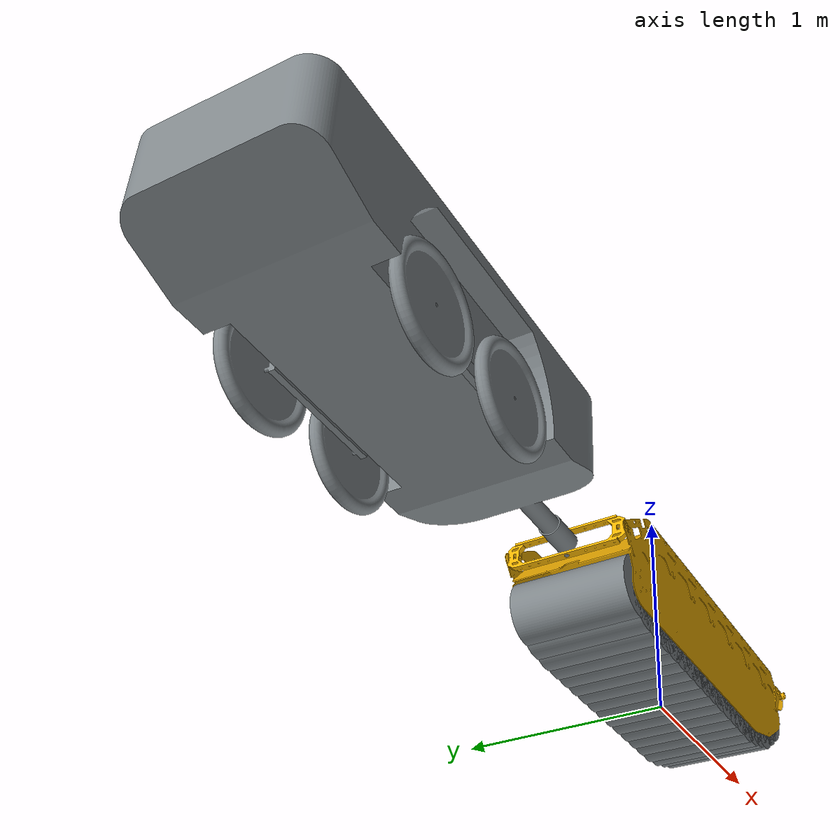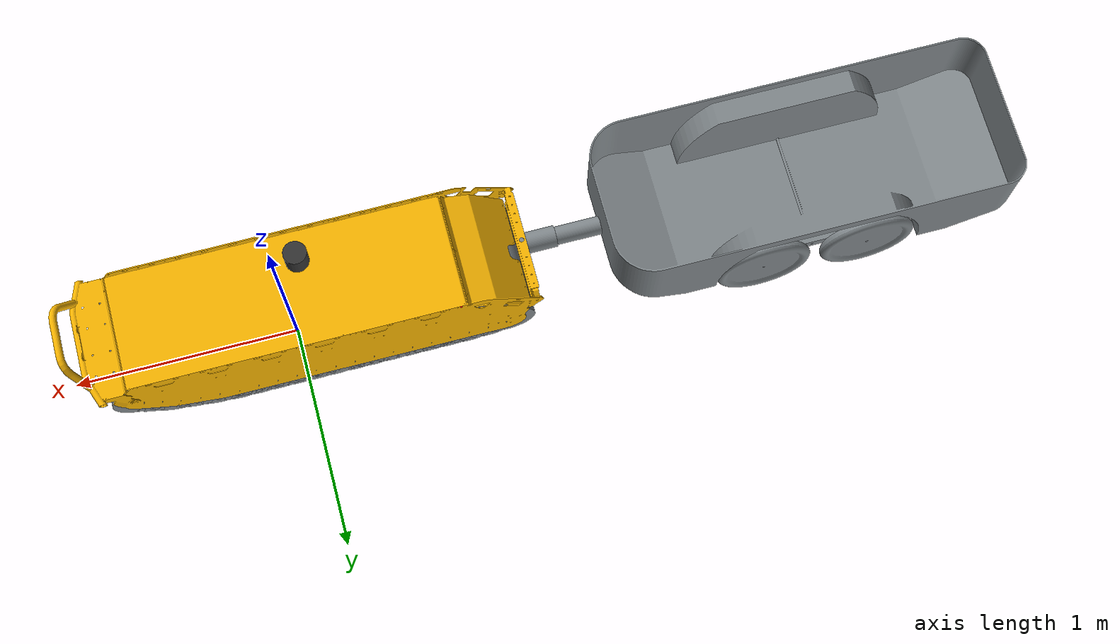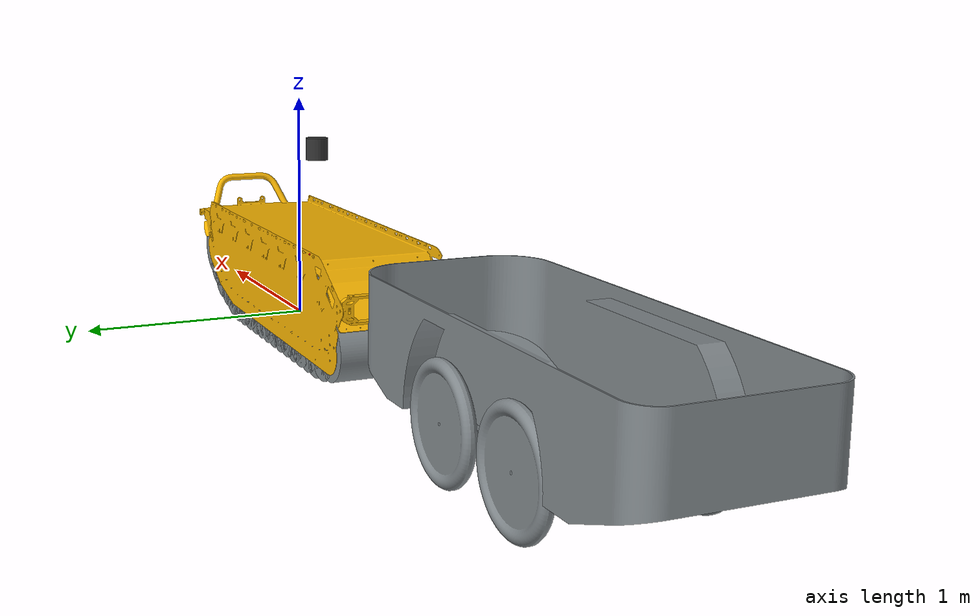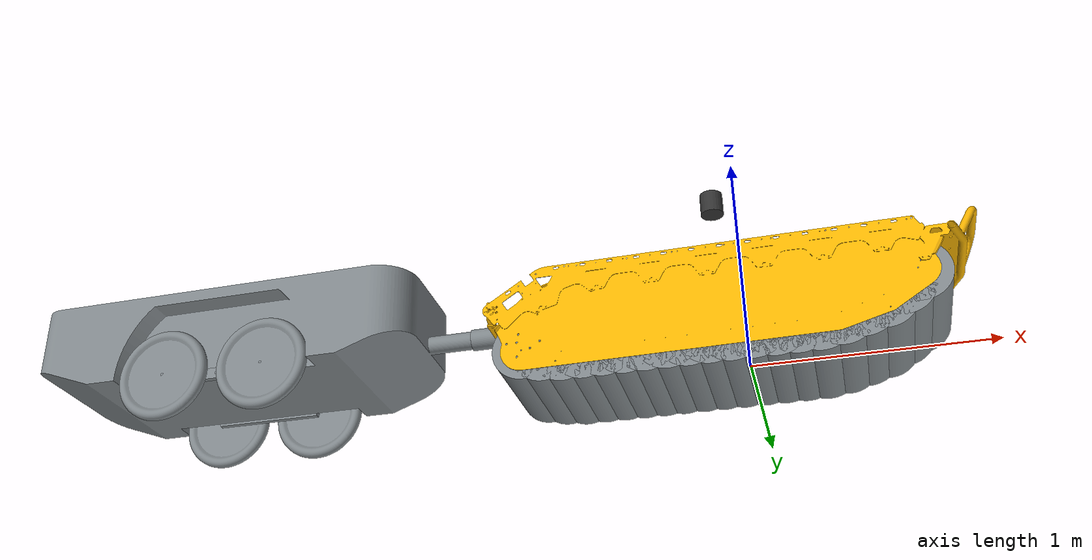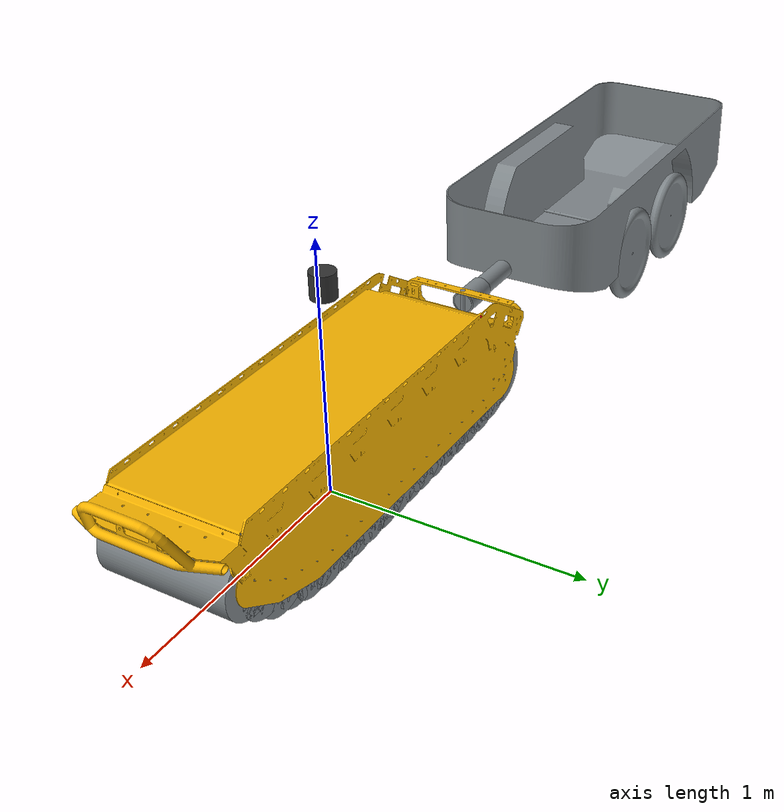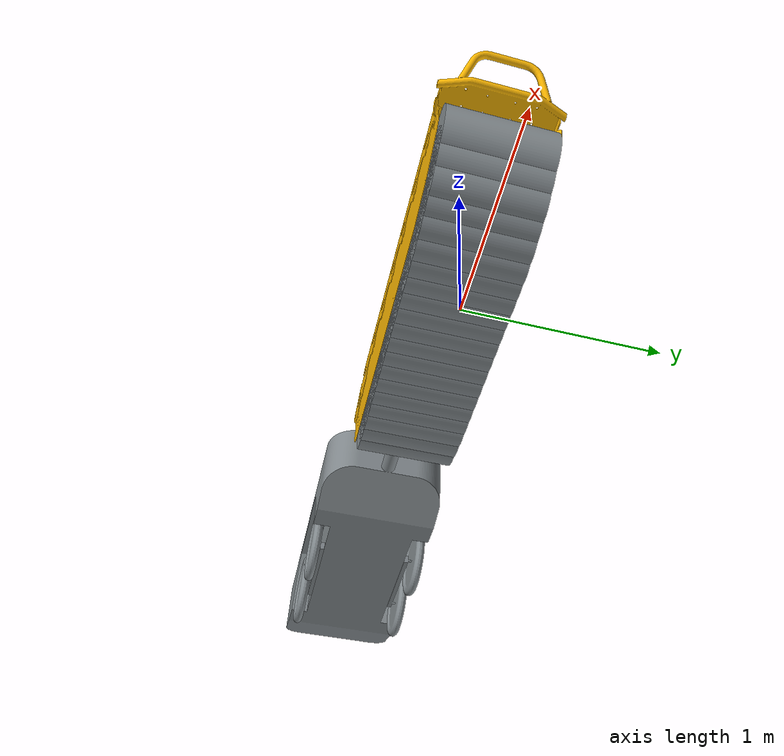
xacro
<?xml version="1.0"?>
<robot name="onshape"  xmlns:xacro="https://www.ros.org/wiki/xacro">

<!-- ── Runtime flags ────────────────────────────────────────────────────── -->
<!-- simulation  : true → include Gazebo sensor plugins + sim-only LiDAR links  -->
<!-- dual_gps    : true → include legacy dual-antenna GPS frames                 -->
<!-- calibration : v1 (pre-displacement) | v2 (post-displacement, run calib first) -->
<xacro:arg name="simulation"  default="false"/>
<xacro:arg name="dual_gps"    default="false"/>
<xacro:arg name="calibration" default="v1"/>
<!-- calib_dir: absolute path to the calibrations/ directory.
     description_calib.launch.py passes the SOURCE tree path so no install-tree
     rebuild is needed after editing calib_*.xacro files. -->
<xacro:arg name="calib_dir"   default="$(find mtt_description)/urdf/calibrations"/>
<xacro:include filename="$(arg calib_dir)/calib_$(arg calibration).xacro"/>

    <xacro:macro name="default_transmission" params="joint_name">
        <transmission name="transmission_${joint_name}">
            <plugin>transmission_interface/SimpleTransmission</plugin>
            <actuator name="actuator_${joint_name}" role="actuator_${joint_name}"/>
            <joint name="${joint_name}" role="${joint_name}">
                <mechanical_reduction>1.0</mechanical_reduction>
            </joint>
        </transmission>
    </xacro:macro>

    <link name="base_footprint"/>

    <link name="base_link">
    <visual>
    <origin xyz="-0.0034808381178577409154 -0.051022168970358453 0.49330103716210749187" rpy="0 -0 ${pi}" />
    <geometry>
    <mesh filename="file://$(find mtt_description)/meshes/visual/m500_ra-02_r02.stl"/>
    </geometry>
    <material name="m500_ra-02_r02_material">
    <color rgba="0.98039215686274505668 0.71372549019607844922 0.0039215686274509803377 1.0"/>
    </material>
    </visual>
    <collision>
    <origin xyz="-0.0034808381178577409154 -0.051022168970358453 0.49330103716210749187" rpy="0 -0 ${pi}" />
    <geometry>
    <mesh filename="file://$(find mtt_description)/meshes/collision/boitecollisionmtt_simple.stl"/>
    </geometry>
    </collision>
    <inertial>
    <origin xyz="-0.077915421490291292272 -0.045505372990426798396 0.20037964466672920638" rpy="0 0 0"/>
    <mass value="150" />
    <inertia ixx="11.048" ixy="0"  ixz="0" iyy="58.2688" iyz="0" izz="63.68" />
    </inertial>
    </link>

   <joint name="base_joint" type="fixed">
    <parent link="base_footprint"/>
    <child link="base_link"/>
    <origin xyz="0 0 -0.1" rpy="0 0 0"/>
    </joint>

    <link name="Rouleau_track_1">
    <visual>
    <origin xyz="0 0 -0.2619375000000000453" rpy="-1.570796326794896558 -7.703719777547410742e-33 0" />
    <geometry>
    <mesh filename="file://$(find mtt_description)/meshes/visual/rouleaufaketrack_525po.stl"/>
    </geometry>
    <material name="rouleaufaketrack_525po_material">
    <color rgba="0.50588235294117644969 0.53333333333333332593 0.54901960784313730279 1.0"/>
    </material>
    </visual>
    <collision>
    <origin xyz="0 0 -0.2619375000000000453" rpy="-1.570796326794896558 -7.703719777547410742e-33 0" />
    <geometry>
    <mesh filename="file://$(find mtt_description)/meshes/visual/rouleaufaketrack_525po.stl"/>
    </geometry>
    </collision>
    <inertial>
    <origin xyz="-9.082983389429123799e-12 -8.2227341536032504615e-12 -0.26193750000873389228" rpy="0 0 0"/>
    <mass value="1.0" />
    <inertia ixx="0.0254" ixy="0"  ixz="0" iyy="0.0254" iyz="0" izz="8.890e-3" />
    </inertial>
    </link>

    <joint name="1_continuous" type="fixed">
    <origin xyz="0.7014675763219452298 -0.30260966897135904707 0.29942602155526376606" rpy="1.570796326794896558 -0 -7.5633943552588769595e-16" />
    <parent link="base_link" />
    <child link="Rouleau_track_1" />
    <axis xyz="0 0 1"/>
    <limit effort="-1" velocity="20" />
    <physics>
    <simbody></simbody>
    <ode>
    <implicit_string_damper>True</implicit_string_damper>
    <fudge_factor>1</fudge_factor>
    </ode>
    <suspension>
    </suspension>
    </physics>
    </joint>

    <link name="Rouleau_track_2">
    <visual>
    <origin xyz="0 0 -0.2619375000000000453" rpy="-1.570796326794896558 -7.703719777547410742e-33 0" />
    <geometry>
    <mesh filename="file://$(find mtt_description)/meshes/visual/rouleaufaketrack_525po.stl"/>
    </geometry>
    <material name="rouleaufaketrack_525po_material">
    <color rgba="0.50588235294117644969 0.53333333333333332593 0.54901960784313730279 1.0"/>
    </material>
    </visual>
    <collision>
    <origin xyz="0 0 -0.2619375000000000453" rpy="-1.570796326794896558 -7.703719777547410742e-33 0" />
    <geometry>
    <mesh filename="file://$(find mtt_description)/meshes/visual/rouleaufaketrack_525po.stl"/>
    </geometry>
    </collision>
    <inertial>
    <origin xyz="-9.082983389429123799e-12 -8.2227341536032504615e-12 -0.26193750000873389228" rpy="0 0 0"/>
    <mass value="1.0" />
    <inertia ixx="0.0254" ixy="0"  ixz="0" iyy="0.0254" iyz="0" izz="8.890e-3" />
    </inertial>
    </link>

    <joint name="2_continuous" type="fixed">
    <origin xyz="0.63021293776953013488 -0.30260966897135899156 0.24925922731169392055" rpy="1.570796326794896558 -0 -7.5633943552588769595e-16" />
    <parent link="base_link" />
    <child link="Rouleau_track_2" />
    <axis xyz="0 0 1"/>
    <limit effort="-1" velocity="20" />
    <physics>
    <simbody></simbody>
    <ode>
    <implicit_string_damper>True</implicit_string_damper>
    <fudge_factor>1</fudge_factor>
    </ode>
    <suspension>
    </suspension>
    </physics>
    </joint>

    <link name="Rouleau_track_3">
    <visual>
    <origin xyz="0 0 -0.2619375000000000453" rpy="-1.570796326794896558 -2.9274135154685984966e-32 0" />
    <geometry>
    <mesh filename="file://$(find mtt_description)/meshes/visual/rouleaufaketrack_525po.stl"/>
    </geometry>
    <material name="rouleaufaketrack_525po_material">
    <color rgba="0.50588235294117644969 0.53333333333333332593 0.54901960784313730279 1.0"/>
    </material>
    </visual>
    <collision>
    <origin xyz="0 0 -0.2619375000000000453" rpy="-1.570796326794896558 -2.9274135154685984966e-32 0" />
    <geometry>
    <mesh filename="file://$(find mtt_description)/meshes/visual/rouleaufaketrack_525po.stl"/>
    </geometry>
    </collision>
    <inertial>
    <origin xyz="-9.082983389429123799e-12 -8.2227341536032504615e-12 -0.26193750000873389228" rpy="0 0 0"/>
    <mass value="1.0" />
    <inertia ixx="0.0254" ixy="0"  ixz="0" iyy="0.0254" iyz="0" izz="8.890e-3" />
    </inertial>
    </link>

    <joint name="3_continuous" type="fixed">
    <origin xyz="0.55767703136521962204 -0.30260966897135893605 0.20171053820694723191" rpy="1.570796326794896558 -0 -7.5633943552588769595e-16" />
    <parent link="base_link" />
    <child link="Rouleau_track_3" />
    <axis xyz="0 0 1"/>
    <limit effort="-1" velocity="20" />
    <physics>
    <simbody></simbody>
    <ode>
    <implicit_string_damper>True</implicit_string_damper>
    <fudge_factor>1</fudge_factor>
    </ode>
    <suspension>
    </suspension>
    </physics>
    </joint>

    <link name="Rouleau_track_4">
    <visual>
    <origin xyz="0 0 -0.2619375000000000453" rpy="-1.570796326794896558 -2.9274135154685984966e-32 0" />
    <geometry>
    <mesh filename="file://$(find mtt_description)/meshes/visual/rouleaufaketrack_525po.stl"/>
    </geometry>
    <material name="rouleaufaketrack_525po_material">
    <color rgba="0.50588235294117644969 0.53333333333333332593 0.54901960784313730279 1.0"/>
    </material>
    </visual>
    <collision>
    <origin xyz="0 0 -0.2619375000000000453" rpy="-1.570796326794896558 -2.9274135154685984966e-32 0" />
    <geometry>
    <mesh filename="file://$(find mtt_description)/meshes/visual/rouleaufaketrack_525po.stl"/>
    </geometry>
    </collision>
    <inertial>
    <origin xyz="-9.082983389429123799e-12 -8.2227341536032504615e-12 -0.26193750000873389228" rpy="0 0 0"/>
    <mass value="1.0" />
    <inertia ixx="0.0254" ixy="0"  ixz="0" iyy="0.0254" iyz="0" izz="8.890e-3" />
    </inertial>
    </link>

    <joint name="4_continuous" type="fixed">
    <origin xyz="0.47434412390430480411 -0.30260966897135888054 0.17622412429685807567" rpy="1.570796326794896558 -0 -7.5633943552588769595e-16" />
    <parent link="base_link" />
    <child link="Rouleau_track_4" />
    <axis xyz="0 0 1"/>
    <limit effort="-1" velocity="20" />
    <physics>
    <simbody></simbody>
    <ode>
    <implicit_string_damper>True</implicit_string_damper>
    <fudge_factor>1</fudge_factor>
    </ode>
    <suspension>
    </suspension>
    </physics>
    </joint>

    <link name="Rouleau_track_5">
    <visual>
    <origin xyz="0 0 -0.2619375000000000453" rpy="-1.570796326794896558 -2.9274135154685984966e-32 0" />
    <geometry>
    <mesh filename="file://$(find mtt_description)/meshes/visual/rouleaufaketrack_525po.stl"/>
    </geometry>
    <material name="rouleaufaketrack_525po_material">
    <color rgba="0.50588235294117644969 0.53333333333333332593 0.54901960784313730279 1.0"/>
    </material>
    </visual>
    <collision>
    <origin xyz="0 0 -0.2619375000000000453" rpy="-1.570796326794896558 -2.9274135154685984966e-32 0" />
    <geometry>
    <mesh filename="file://$(find mtt_description)/meshes/visual/rouleaufaketrack_525po.stl"/>
    </geometry>
    </collision>
    <inertial>
    <origin xyz="-9.082983389429123799e-12 -8.2227341536032504615e-12 -0.26193750000873389228" rpy="0 0 0"/>
    <mass value="1.0" />
    <inertia ixx="0.0254" ixy="0"  ixz="0" iyy="0.0254" iyz="0" izz="8.890e-3" />
    </inertial>
    </link>

    <joint name="5_continuous" type="fixed">
    <origin xyz="0.39101121644338021621 -0.30260966897135876952 0.15073771038676886391" rpy="1.570796326794896558 -0 -7.5633943552588769595e-16" />
    <parent link="base_link" />
    <child link="Rouleau_track_5" />
    <axis xyz="0 0 1"/>
    <limit effort="-1" velocity="20" />
    <physics>
    <simbody></simbody>
    <ode>
    <implicit_string_damper>True</implicit_string_damper>
    <fudge_factor>1</fudge_factor>
    </ode>
    <suspension>
    </suspension>
    </physics>
    </joint>

    <link name="Rouleau_track_6">
    <visual>
    <origin xyz="0 0 -0.2619375000000000453" rpy="-1.570796326794896558 -2.9274135154685984966e-32 0" />
    <geometry>
    <mesh filename="file://$(find mtt_description)/meshes/visual/rouleaufaketrack_525po.stl"/>
    </geometry>
    <material name="rouleaufaketrack_525po_material">
    <color rgba="0.50588235294117644969 0.53333333333333332593 0.54901960784313730279 1.0"/>
    </material>
    </visual>
    <collision>
    <origin xyz="0 0 -0.2619375000000000453" rpy="-1.570796326794896558 -2.9274135154685984966e-32 0" />
    <geometry>
    <mesh filename="file://$(find mtt_description)/meshes/visual/rouleaufaketrack_525po.stl"/>
    </geometry>
    </collision>
    <inertial>
    <origin xyz="-9.082983389429123799e-12 -8.2227341536032504615e-12 -0.26193750000873389228" rpy="0 0 0"/>
    <mass value="1.0" />
    <inertia ixx="0.0254" ixy="0"  ixz="0" iyy="0.0254" iyz="0" izz="8.890e-3" />
    </inertial>
    </link>

    <joint name="6_continuous" type="fixed">
    <origin xyz="0.30589785624702453548 -0.30260966897135871401 0.13716525069048957075" rpy="1.570796326794896558 -0 -7.5633943552588769595e-16" />
    <parent link="base_link" />
    <child link="Rouleau_track_6" />
    <axis xyz="0 0 1"/>
    <limit effort="-1" velocity="20" />
    <physics>
    <simbody></simbody>
    <ode>
    <implicit_string_damper>True</implicit_string_damper>
    <fudge_factor>1</fudge_factor>
    </ode>
    <suspension>
    </suspension>
    </physics>
    </joint>

    <link name="Rouleau_track_7">
    <visual>
    <origin xyz="5.5511151231257827021e-17 0 -0.2619375000000000453" rpy="-1.570796326794896558 -2.9274135154685984966e-32 0" />
    <geometry>
    <mesh filename="file://$(find mtt_description)/meshes/visual/rouleaufaketrack_525po.stl"/>
    </geometry>
    <material name="rouleaufaketrack_525po_material">
    <color rgba="0.50588235294117644969 0.53333333333333332593 0.54901960784313730279 1.0"/>
    </material>
    </visual>
    <collision>
    <origin xyz="5.5511151231257827021e-17 0 -0.2619375000000000453" rpy="-1.570796326794896558 -2.9274135154685984966e-32 0" />
    <geometry>
    <mesh filename="file://$(find mtt_description)/meshes/visual/rouleaufaketrack_525po.stl"/>
    </geometry>
    </collision>
    <inertial>
    <origin xyz="-9.0829278782778925411e-12 -8.2227341536032504615e-12 -0.26193750000873389228" rpy="0 0 0"/>
    <mass value="1.0" />
    <inertia ixx="0.0254" ixy="0"  ixz="0" iyy="0.0254" iyz="0" izz="8.890e-3" />
    </inertial>
    </link>

    <joint name="7_continuous" type="fixed">
    <origin xyz="0.21875469438405417688 -0.3026096689713586585 0.13717527124629197433" rpy="1.570796326794896558 -0 -7.5633943552588769595e-16" />
    <parent link="base_link" />
    <child link="Rouleau_track_7" />
    <axis xyz="0 0 1"/>
    <limit effort="-1" velocity="20" />
    <physics>
    <simbody></simbody>
    <ode>
    <implicit_string_damper>True</implicit_string_damper>
    <fudge_factor>1</fudge_factor>
    </ode>
    <suspension>
    </suspension>
    </physics>
    </joint>

    <link name="Rouleau_track_8">
    <visual>
    <origin xyz="5.5511151231257827021e-17 0 -0.2619375000000000453" rpy="-1.570796326794896558 -2.9274135154685984966e-32 0" />
    <geometry>
    <mesh filename="file://$(find mtt_description)/meshes/visual/rouleaufaketrack_525po.stl"/>
    </geometry>
    <material name="rouleaufaketrack_525po_material">
    <color rgba="0.50588235294117644969 0.53333333333333332593 0.54901960784313730279 1.0"/>
    </material>
    </visual>
    <collision>
    <origin xyz="5.5511151231257827021e-17 0 -0.2619375000000000453" rpy="-1.570796326794896558 -2.9274135154685984966e-32 0" />
    <geometry>
    <mesh filename="file://$(find mtt_description)/meshes/visual/rouleaufaketrack_525po.stl"/>
    </geometry>
    </collision>
    <inertial>
    <origin xyz="-9.0829278782778925411e-12 -8.2227341536032504615e-12 -0.26193750000873389228" rpy="0 0 0"/>
    <mass value="1.0" />
    <inertia ixx="0.0254" ixy="0"  ixz="0" iyy="0.0254" iyz="0" izz="8.890e-3" />
    </inertial>
    </link>

    <joint name="8_continuous" type="fixed">
    <origin xyz="0.13161153252108562239 -0.3026096689713586585 0.13718529180209448892" rpy="1.570796326794896558 -0 -7.5633943552588769595e-16" />
    <parent link="base_link" />
    <child link="Rouleau_track_8" />
    <axis xyz="0 0 1"/>
    <limit effort="-1" velocity="20" />
    <physics>
    <simbody></simbody>
    <ode>
    <implicit_string_damper>True</implicit_string_damper>
    <fudge_factor>1</fudge_factor>
    </ode>
    <suspension>
    </suspension>
    </physics>
    </joint>

    <link name="Rouleau_track_9">
    <visual>
    <origin xyz="5.5511151231257827021e-17 0 -0.2619375000000000453" rpy="-1.570796326794896558 -2.9274135154685984966e-32 0" />
    <geometry>
    <mesh filename="file://$(find mtt_description)/meshes/visual/rouleaufaketrack_525po.stl"/>
    </geometry>
    <material name="rouleaufaketrack_525po_material">
    <color rgba="0.50588235294117644969 0.53333333333333332593 0.54901960784313730279 1.0"/>
    </material>
    </visual>
    <collision>
    <origin xyz="5.5511151231257827021e-17 0 -0.2619375000000000453" rpy="-1.570796326794896558 -2.9274135154685984966e-32 0" />
    <geometry>
    <mesh filename="file://$(find mtt_description)/meshes/visual/rouleaufaketrack_525po.stl"/>
    </geometry>
    </collision>
    <inertial>
    <origin xyz="-9.0829278782778925411e-12 -8.2227341536032504615e-12 -0.26193750000873389228" rpy="0 0 0"/>
    <mass value="1.0" />
    <inertia ixx="0.0254" ixy="0"  ixz="0" iyy="0.0254" iyz="0" izz="8.890e-3" />
    </inertial>
    </link>

    <joint name="9_continuous" type="fixed">
    <origin xyz="0.044468370658119274474 -0.30260966897135854747 0.13719531235789694801" rpy="1.570796326794896558 -0 -7.5633943552588769595e-16" />
    <parent link="base_link" />
    <child link="Rouleau_track_9" />
    <axis xyz="0 0 1"/>
    <limit effort="-1" velocity="20" />
    <physics>
    <simbody></simbody>
    <ode>
    <implicit_string_damper>True</implicit_string_damper>
    <fudge_factor>1</fudge_factor>
    </ode>
    <suspension>
    </suspension>
    </physics>
    </joint>

    <link name="Rouleau_track_10">
    <visual>
    <origin xyz="-2.7755575615628913511e-17 0 -0.2619375000000000453" rpy="-1.570796326794896558 -2.9274135154685984966e-32 0" />
    <geometry>
    <mesh filename="file://$(find mtt_description)/meshes/visual/rouleaufaketrack_525po.stl"/>
    </geometry>
    <material name="rouleaufaketrack_525po_material">
    <color rgba="0.50588235294117644969 0.53333333333333332593 0.54901960784313730279 1.0"/>
    </material>
    </visual>
    <collision>
    <origin xyz="-2.7755575615628913511e-17 0 -0.2619375000000000453" rpy="-1.570796326794896558 -2.9274135154685984966e-32 0" />
    <geometry>
    <mesh filename="file://$(find mtt_description)/meshes/visual/rouleaufaketrack_525po.stl"/>
    </geometry>
    </collision>
    <inertial>
    <origin xyz="-9.0830111450047394279e-12 -8.2227341536032504615e-12 -0.26193750000873389228" rpy="0 0 0"/>
    <mass value="1.0" />
    <inertia ixx="0.0254" ixy="0"  ixz="0" iyy="0.0254" iyz="0" izz="8.890e-3" />
    </inertial>
    </link>

    <joint name="10_continuous" type="fixed">
    <origin xyz="-0.042674791204848093462 -0.30260966897135843645 0.13720533291369940709" rpy="1.570796326794896558 -0 -7.5633943552588769595e-16" />
    <parent link="base_link" />
    <child link="Rouleau_track_10" />
    <axis xyz="0 0 1"/>
    <limit effort="-1" velocity="20" />
    <physics>
    <simbody></simbody>
    <ode>
    <implicit_string_damper>True</implicit_string_damper>
    <fudge_factor>1</fudge_factor>
    </ode>
    <suspension>
    </suspension>
    </physics>
    </joint>

    <link name="Rouleau_track_11">
    <visual>
    <origin xyz="-2.7755575615628913511e-17 0 -0.2619375000000000453" rpy="-1.570796326794896558 -2.9274135154685984966e-32 0" />
    <geometry>
    <mesh filename="file://$(find mtt_description)/meshes/visual/rouleaufaketrack_525po.stl"/>
    </geometry>
    <material name="rouleaufaketrack_525po_material">
    <color rgba="0.50588235294117644969 0.53333333333333332593 0.54901960784313730279 1.0"/>
    </material>
    </visual>
    <collision>
    <origin xyz="-2.7755575615628913511e-17 0 -0.2619375000000000453" rpy="-1.570796326794896558 -2.9274135154685984966e-32 0" />
    <geometry>
    <mesh filename="file://$(find mtt_description)/meshes/visual/rouleaufaketrack_525po.stl"/>
    </geometry>
    </collision>
    <inertial>
    <origin xyz="-9.0830111450047394279e-12 -8.2227341536032504615e-12 -0.26193750000873389228" rpy="0 0 0"/>
    <mass value="1.0" />
    <inertia ixx="0.0254" ixy="0"  ixz="0" iyy="0.0254" iyz="0" izz="8.890e-3" />
    </inertial>
    </link>

    <joint name="11_continuous" type="fixed">
    <origin xyz="-0.12981795306781560018 -0.30260966897135843645 0.13721535346950286538" rpy="1.570796326794896558 -0 -7.5633943552588769595e-16" />
    <parent link="base_link" />
    <child link="Rouleau_track_11" />
    <axis xyz="0 0 1"/>
    <limit effort="-1" velocity="20" />
    <physics>
    <simbody></simbody>
    <ode>
    <implicit_string_damper>True</implicit_string_damper>
    <fudge_factor>1</fudge_factor>
    </ode>
    <suspension>
    </suspension>
    </physics>
    </joint>

    <link name="Rouleau_track_12">
    <visual>
    <origin xyz="0 0 -0.2619375000000000453" rpy="-1.570796326794896558 -2.9274135154685984966e-32 0" />
    <geometry>
    <mesh filename="file://$(find mtt_description)/meshes/visual/rouleaufaketrack_525po.stl"/>
    </geometry>
    <material name="rouleaufaketrack_525po_material">
    <color rgba="0.50588235294117644969 0.53333333333333332593 0.54901960784313730279 1.0"/>
    </material>
    </visual>
    <collision>
    <origin xyz="0 0 -0.2619375000000000453" rpy="-1.570796326794896558 -2.9274135154685984966e-32 0" />
    <geometry>
    <mesh filename="file://$(find mtt_description)/meshes/visual/rouleaufaketrack_525po.stl"/>
    </geometry>
    </collision>
    <inertial>
    <origin xyz="-9.082983389429123799e-12 -8.2227341536032504615e-12 -0.26193750000873389228" rpy="0 0 0"/>
    <mass value="1.0" />
    <inertia ixx="0.0254" ixy="0"  ixz="0" iyy="0.0254" iyz="0" izz="8.890e-3" />
    </inertial>
    </link>

    <joint name="12_continuous" type="fixed">
    <origin xyz="-0.21696111493078301669 -0.30260966897135832543 0.13722537402530532447" rpy="1.570796326794896558 -0 -7.5633943552588769595e-16" />
    <parent link="base_link" />
    <child link="Rouleau_track_12" />
    <axis xyz="0 0 1"/>
    <limit effort="-1" velocity="20" />
    <physics>
    <simbody></simbody>
    <ode>
    <implicit_string_damper>True</implicit_string_damper>
    <fudge_factor>1</fudge_factor>
    </ode>
    <suspension>
    </suspension>
    </physics>
    </joint>

    <link name="Rouleau_track_13">
    <visual>
    <origin xyz="0 0 -0.26193750000000010081" rpy="-1.570796326794896558 -2.9274135154685984966e-32 0" />
    <geometry>
    <mesh filename="file://$(find mtt_description)/meshes/visual/rouleaufaketrack_525po.stl"/>
    </geometry>
    <material name="rouleaufaketrack_525po_material">
    <color rgba="0.50588235294117644969 0.53333333333333332593 0.54901960784313730279 1.0"/>
    </material>
    </visual>
    <collision>
    <origin xyz="0 0 -0.26193750000000010081" rpy="-1.570796326794896558 -2.9274135154685984966e-32 0" />
    <geometry>
    <mesh filename="file://$(find mtt_description)/meshes/visual/rouleaufaketrack_525po.stl"/>
    </geometry>
    </collision>
    <inertial>
    <origin xyz="-9.082983389429123799e-12 -8.2227341536032504615e-12 -0.26193750000873394779" rpy="0 0 0"/>
    <mass value="1.0" />
    <inertia ixx="0.0254" ixy="0"  ixz="0" iyy="0.0254" iyz="0" izz="8.890e-3" />
    </inertial>
    </link>

    <joint name="13_continuous" type="fixed">
    <origin xyz="-0.30410427679375034993 -0.30260966897135821441 0.13723539458110778355" rpy="1.570796326794896558 -0 -7.5633943552588769595e-16" />
    <parent link="base_link" />
    <child link="Rouleau_track_13" />
    <axis xyz="0 0 1"/>
    <limit effort="-1" velocity="20" />
    <physics>
    <simbody></simbody>
    <ode>
    <implicit_string_damper>True</implicit_string_damper>
    <fudge_factor>1</fudge_factor>
    </ode>
    <suspension>
    </suspension>
    </physics>
    </joint>

    <link name="Rouleau_track_14">
    <visual>
    <origin xyz="-2.7755575615628913511e-17 0 -0.2619375000000000453" rpy="-1.570796326794896558 -2.9274135154685984966e-32 0" />
    <geometry>
    <mesh filename="file://$(find mtt_description)/meshes/visual/rouleaufaketrack_525po.stl"/>
    </geometry>
    <material name="rouleaufaketrack_525po_material">
    <color rgba="0.50588235294117644969 0.53333333333333332593 0.54901960784313730279 1.0"/>
    </material>
    </visual>
    <collision>
    <origin xyz="-2.7755575615628913511e-17 0 -0.2619375000000000453" rpy="-1.570796326794896558 -2.9274135154685984966e-32 0" />
    <geometry>
    <mesh filename="file://$(find mtt_description)/meshes/visual/rouleaufaketrack_525po.stl"/>
    </geometry>
    </collision>
    <inertial>
    <origin xyz="-9.0830111450047394279e-12 -8.2227341536032504615e-12 -0.26193750000873389228" rpy="0 0 0"/>
    <mass value="1.0" />
    <inertia ixx="0.0254" ixy="0"  ixz="0" iyy="0.0254" iyz="0" izz="8.890e-3" />
    </inertial>
    </link>

    <joint name="14_continuous" type="fixed">
    <origin xyz="-0.39124743865671768317 -0.30260966897135821441 0.13724541513691029815" rpy="1.570796326794896558 -0 -7.5633943552588769595e-16" />
    <parent link="base_link" />
    <child link="Rouleau_track_14" />
    <axis xyz="0 0 1"/>
    <limit effort="-1" velocity="20" />
    <physics>
    <simbody></simbody>
    <ode>
    <implicit_string_damper>True</implicit_string_damper>
    <fudge_factor>1</fudge_factor>
    </ode>
    <suspension>
    </suspension>
    </physics>
    </joint>

    <link name="Rouleau_track_15">
    <visual>
    <origin xyz="-2.7755575615628913511e-17 0 -0.2619375000000000453" rpy="-1.570796326794896558 -2.9274135154685984966e-32 0" />
    <geometry>
    <mesh filename="file://$(find mtt_description)/meshes/visual/rouleaufaketrack_525po.stl"/>
    </geometry>
    <material name="rouleaufaketrack_525po_material">
    <color rgba="0.50588235294117644969 0.53333333333333332593 0.54901960784313730279 1.0"/>
    </material>
    </visual>
    <collision>
    <origin xyz="-2.7755575615628913511e-17 0 -0.2619375000000000453" rpy="-1.570796326794896558 -2.9274135154685984966e-32 0" />
    <geometry>
    <mesh filename="file://$(find mtt_description)/meshes/visual/rouleaufaketrack_525po.stl"/>
    </geometry>
    </collision>
    <inertial>
    <origin xyz="-9.0830111450047394279e-12 -8.2227341536032504615e-12 -0.26193750000873389228" rpy="0 0 0"/>
    <mass value="1.0" />
    <inertia ixx="0.0254" ixy="0"  ixz="0" iyy="0.0254" iyz="0" izz="8.890e-3" />
    </inertial>
    </link>

    <joint name="15_continuous" type="fixed">
    <origin xyz="-0.47839060051968412823 -0.30260966897135821441 0.13725543569271270172" rpy="1.570796326794896558 -0 -7.5633943552588769595e-16" />
    <parent link="base_link" />
    <child link="Rouleau_track_15" />
    <axis xyz="0 0 1"/>
    <limit effort="-1" velocity="20" />
    <physics>
    <simbody></simbody>
    <ode>
    <implicit_string_damper>True</implicit_string_damper>
    <fudge_factor>1</fudge_factor>
    </ode>
    <suspension>
    </suspension>
    </physics>
    </joint>

    <link name="Rouleau_track_16">
    <visual>
    <origin xyz="5.5511151231257827021e-17 0 -0.2619375000000000453" rpy="-1.570796326794896558 -2.9274135154685984966e-32 0" />
    <geometry>
    <mesh filename="file://$(find mtt_description)/meshes/visual/rouleaufaketrack_525po.stl"/>
    </geometry>
    <material name="rouleaufaketrack_525po_material">
    <color rgba="0.50588235294117644969 0.53333333333333332593 0.54901960784313730279 1.0"/>
    </material>
    </visual>
    <collision>
    <origin xyz="5.5511151231257827021e-17 0 -0.2619375000000000453" rpy="-1.570796326794896558 -2.9274135154685984966e-32 0" />
    <geometry>
    <mesh filename="file://$(find mtt_description)/meshes/visual/rouleaufaketrack_525po.stl"/>
    </geometry>
    </collision>
    <inertial>
    <origin xyz="-9.0829278782778925411e-12 -8.2227341536032504615e-12 -0.26193750000873389228" rpy="0 0 0"/>
    <mass value="1.0" />
    <inertia ixx="0.0254" ixy="0"  ixz="0" iyy="0.0254" iyz="0" izz="8.890e-3" />
    </inertial>
    </link>

    <joint name="16_continuous" type="fixed">
    <origin xyz="-0.56553376238265151699 -0.30260966897135799236 0.13726545624851521632" rpy="1.570796326794896558 -0 -7.5633943552588769595e-16" />
    <parent link="base_link" />
    <child link="Rouleau_track_16" />
    <axis xyz="0 0 1"/>
    <limit effort="-1" velocity="20" />
    <physics>
    <simbody></simbody>
    <ode>
    <implicit_string_damper>True</implicit_string_damper>
    <fudge_factor>1</fudge_factor>
    </ode>
    <suspension>
    </suspension>
    </physics>
    </joint>

    <link name="Rouleau_track_17">
    <visual>
    <origin xyz="5.5511151231257827021e-17 0 -0.2619375000000000453" rpy="-1.570796326794896558 -2.9274135154685984966e-32 0" />
    <geometry>
    <mesh filename="file://$(find mtt_description)/meshes/visual/rouleaufaketrack_525po.stl"/>
    </geometry>
    <material name="rouleaufaketrack_525po_material">
    <color rgba="0.50588235294117644969 0.53333333333333332593 0.54901960784313730279 1.0"/>
    </material>
    </visual>
    <collision>
    <origin xyz="5.5511151231257827021e-17 0 -0.2619375000000000453" rpy="-1.570796326794896558 -2.9274135154685984966e-32 0" />
    <geometry>
    <mesh filename="file://$(find mtt_description)/meshes/visual/rouleaufaketrack_525po.stl"/>
    </geometry>
    </collision>
    <inertial>
    <origin xyz="-9.0829278782778925411e-12 -8.2227341536032504615e-12 -0.26193750000873389228" rpy="0 0 0"/>
    <mass value="1.0" />
    <inertia ixx="0.0254" ixy="0"  ixz="0" iyy="0.0254" iyz="0" izz="8.890e-3" />
    </inertial>
    </link>

    <joint name="17_continuous" type="fixed">
    <origin xyz="-0.65267692424561885023 -0.30260966897135799236 0.13727547680431761989" rpy="1.570796326794896558 -0 -7.5633943552588769595e-16" />
    <parent link="base_link" />
    <child link="Rouleau_track_17" />
    <axis xyz="0 0 1"/>
    <limit effort="-1" velocity="20" />
    <physics>
    <simbody></simbody>
    <ode>
    <implicit_string_damper>True</implicit_string_damper>
    <fudge_factor>1</fudge_factor>
    </ode>
    <suspension>
    </suspension>
    </physics>
    </joint>

    <link name="Rouleau_track_18">
    <visual>
    <origin xyz="5.5511151231257827021e-17 0 -0.26193750000000010081" rpy="-1.570796326794896558 -2.9274135154685984966e-32 0" />
    <geometry>
    <mesh filename="file://$(find mtt_description)/meshes/visual/rouleaufaketrack_525po.stl"/>
    </geometry>
    <material name="rouleaufaketrack_525po_material">
    <color rgba="0.50588235294117644969 0.53333333333333332593 0.54901960784313730279 1.0"/>
    </material>
    </visual>
    <collision>
    <origin xyz="5.5511151231257827021e-17 0 -0.26193750000000010081" rpy="-1.570796326794896558 -2.9274135154685984966e-32 0" />
    <geometry>
    <mesh filename="file://$(find mtt_description)/meshes/visual/rouleaufaketrack_525po.stl"/>
    </geometry>
    </collision>
    <inertial>
    <origin xyz="-9.0829278782778925411e-12 -8.2227341536032504615e-12 -0.26193750000873394779" rpy="0 0 0"/>
    <mass value="1.0" />
    <inertia ixx="0.0254" ixy="0"  ixz="0" iyy="0.0254" iyz="0" izz="8.890e-3" />
    </inertial>
    </link>

    <joint name="18_continuous" type="fixed">
    <origin xyz="-0.73982008610858640552 -0.30260966897135788134 0.13728549736012013449" rpy="1.570796326794896558 -0 -7.5633943552588769595e-16" />
    <parent link="base_link" />
    <child link="Rouleau_track_18" />
    <axis xyz="0 0 1"/>
    <limit effort="-1" velocity="20" />
    <physics>
    <simbody></simbody>
    <ode>
    <implicit_string_damper>True</implicit_string_damper>
    <fudge_factor>1</fudge_factor>
    </ode>
    <suspension>
    </suspension>
    </physics>
    </joint>

    <link name="Rouleau_track_19">
    <visual>
    <origin xyz="0 0 -0.2619375000000000453" rpy="-1.570796326794896558 -2.9274135154685984966e-32 0" />
    <geometry>
    <mesh filename="file://$(find mtt_description)/meshes/visual/rouleaufaketrack_525po.stl"/>
    </geometry>
    <material name="rouleaufaketrack_525po_material">
    <color rgba="0.50588235294117644969 0.53333333333333332593 0.54901960784313730279 1.0"/>
    </material>
    </visual>
    <collision>
    <origin xyz="0 0 -0.2619375000000000453" rpy="-1.570796326794896558 -2.9274135154685984966e-32 0" />
    <geometry>
    <mesh filename="file://$(find mtt_description)/meshes/visual/rouleaufaketrack_525po.stl"/>
    </geometry>
    </collision>
    <inertial>
    <origin xyz="-9.082983389429123799e-12 -8.2227341536032504615e-12 -0.26193750000873389228" rpy="0 0 0"/>
    <mass value="1.0" />
    <inertia ixx="0.0254" ixy="0"  ixz="0" iyy="0.0254" iyz="0" izz="8.890e-3" />
    </inertial>
    </link>

    <joint name="19_continuous" type="fixed">
    <origin xyz="-0.82595460894701899779 -0.30260966897135777032 0.14666682073043030288" rpy="1.570796326794896558 -0 -7.5633943552588769595e-16" />
    <parent link="base_link" />
    <child link="Rouleau_track_19" />
    <axis xyz="0 0 1"/>
    <limit effort="-1" velocity="20" />
    <physics>
    <simbody></simbody>
    <ode>
    <implicit_string_damper>True</implicit_string_damper>
    <fudge_factor>1</fudge_factor>
    </ode>
    <suspension>
    </suspension>
    </physics>
    </joint>

    <link name="Rouleau_track_20">
    <visual>
    <origin xyz="0 -1.3877787807814456755e-17 -0.2619375000000000453" rpy="-1.570796326794896558 1.0785207688568652149e-32 0" />
    <geometry>
    <mesh filename="file://$(find mtt_description)/meshes/visual/rouleaufaketrack_525po.stl"/>
    </geometry>
    <material name="rouleaufaketrack_525po_material">
    <color rgba="0.50588235294117644969 0.53333333333333332593 0.54901960784313730279 1.0"/>
    </material>
    </visual>
    <collision>
    <origin xyz="0 -1.3877787807814456755e-17 -0.2619375000000000453" rpy="-1.570796326794896558 1.0785207688568652149e-32 0" />
    <geometry>
    <mesh filename="file://$(find mtt_description)/meshes/visual/rouleaufaketrack_525po.stl"/>
    </geometry>
    </collision>
    <inertial>
    <origin xyz="-9.082983389429123799e-12 -8.2227480313910582759e-12 -0.26193750000873389228" rpy="0 0 0"/>
    <mass value="1.0" />
    <inertia ixx="0.0254" ixy="0"  ixz="0" iyy="0.0254" iyz="0" izz="8.890e-3" />
    </inertial>
    </link>

    <joint name="20_continuous" type="fixed">
    <origin xyz="-0.91110403062049183376 -0.30260966897135777032 0.16520075578373016878" rpy="1.570796326794896558 -0 -7.5633943552588769595e-16" />
    <parent link="base_link" />
    <child link="Rouleau_track_20" />
    <axis xyz="0 0 1"/>
    <limit effort="-1" velocity="20" />
    <physics>
    <simbody></simbody>
    <ode>
    <implicit_string_damper>True</implicit_string_damper>
    <fudge_factor>1</fudge_factor>
    </ode>
    <suspension>
    </suspension>
    </physics>
    </joint>

    <link name="Frame_fixation_articule">
    <visual>
    <origin xyz="0 0 -0.26352500000102996314" rpy="1.570796326794896558 2.9274135154685984966e-32 0" />
    <geometry>
    <mesh filename="file://$(find mtt_description)/meshes/visual/m500_fa-f-01_r00.stl"/>
    </geometry>
    <material name="m500_fa-f-01_r00_material">
    <color rgba="0.98039215686274505668 0.71372549019607844922 0.0039215686274509803377 1.0"/>
    </material>
    </visual>
    <collision>
    <origin xyz="0 0 -0.26352500000102996314" rpy="1.570796326794896558 2.9274135154685984966e-32 0" />
    <geometry>
    <mesh filename="file://$(find mtt_description)/meshes/visual/m500_fa-f-01_r00.stl"/>
    </geometry>
    </collision>
    <inertial>
    <origin xyz="-3.9892756405493079145e-11 -1.1475286443859219259e-10 -0.26817516801928165115" rpy="0 0 0"/>
    <mass value="4.2856980941026048271" />
    <inertia ixx="0.15081833822080548124" ixy="-3.1493952847483546326e-14"  ixz="-2.7291301433546465536e-09" iyy="0.14291517499876990605" iyz="4.1782617806359028221e-10" izz="0.0087729760408515339992" />
    </inertial>
    </link>

    <link name="joint_remorque_simple">
    <visual>
    <origin xyz="0 0 -0.11429999999970297253" rpy="3.141592653589793116 1.0947644252537633367e-47 2.4651903288156618919e-32" />
    <geometry>
    <mesh filename="file://$(find mtt_description)/meshes/visual/joint_remorque_simple.stl"/>
    </geometry>
    <material name="joint_remorque_simple_material">
    <color rgba="0.50588235294117644969 0.53333333333333332593 0.54901960784313730279 1.0"/>
    </material>
    </visual>
    <collision>
    <origin xyz="0 0 -0.11429999999970297253" rpy="3.141592653589793116 1.0947644252537633367e-47 2.4651903288156618919e-32" />
    <geometry>
    <mesh filename="file://$(find mtt_description)/meshes/visual/joint_remorque_simple.stl"/>
    </geometry>
    </collision>
    <inertial>
    <origin xyz="-0.066649078397283970099 -1.3264048723360915067e-08 -0.057149999999851569532" rpy="0 0 0"/>
    <mass value="2.4244944218593222907" />
    <inertia ixx="0.0045362397987309356281" ixy="2.7180197249639030826e-09"  ixz="2.2800525023181053727e-41" iyy="0.0080855686635830838899" iyz="-9.2489917741012919164e-10" izz="0.0077799714228289117493" />
    </inertial>
    </link>

    <link name="MTT_remorque">
    <visual>
    <origin xyz="0 0 0" rpy="-1.570796326794896558 -2.9274135154686072548e-32 0" />
    <geometry>
    <mesh filename="file://$(find mtt_description)/meshes/visual/remorquegrise_corps.stl"/>
    </geometry>
    <material name="remorquegrise_corps_material">
    <color rgba="0.50588235294117644969 0.53333333333333332593 0.54901960784313730279 1.0"/>
    </material>
    </visual>
    <collision>
    <origin xyz="0 0 0" rpy="-1.570796326794896558 -2.9274135154686072548e-32 0" />
    <geometry>
    <mesh filename="file://$(find mtt_description)/meshes/collision/remorquegrise_collision.stl"/>
    </geometry>
    </collision>
    <inertial>
    <origin xyz="-1.3754218481959806043e-07 0.0034236501170869263963 -1.2492342427482756584" rpy="0 0 0"/>
    <mass value="75" />
    <inertia ixx="19.61" ixy="1.9694375352015794851e-06"  ixz="3.4143802835478518731e-05" iyy="22.119" iyz="0.08948044734924905097" izz="4.369" />
    </inertial>
    </link>

    <link name="Remorque_lien_roue_gauche">
    <visual>
    <origin xyz="-0.4699000000010151723 -0.014477999967073801324 -0.025400000000000005906" rpy="0 2.9274135154685984966e-32 0" />
    <geometry>
    <mesh filename="file://$(find mtt_description)/meshes/visual/remorquebarrelienroues.stl"/>
    </geometry>
    <material name="remorquebarrelienroues_material">
    <color rgba="0.50588235294117644969 0.53333333333333332593 0.54901960784313730279 1.0"/>
    </material>
    </visual>
    <collision>
    <origin xyz="-0.4699000000010151723 -0.014477999967073801324 -0.025400000000000005906" rpy="0 2.9274135154685984966e-32 0" />
    <geometry>
    <mesh filename="file://$(find mtt_description)/meshes/visual/remorquebarrelienroues.stl"/>
    </geometry>
    </collision>
    <inertial>
    <origin xyz="-2.2204460492503130808e-16 -1.7347234759768070944e-18 -0.011962764931897929346" rpy="0 0 0"/>
    <mass value="1.0" />
    <inertia ixx="0.0015481614309977712648" ixy="0"  ixz="3.398701470065399431e-33" iyy="0.11698078969574195185" iyz="0" izz="0.11764728620809132564" />
    </inertial>
    </link>

    <link name="remorque_roue_FL">
    <visual>
    <origin xyz="0 -3.3306690738754696213e-16 0" rpy="0 2.9274135154685984966e-32 0" />
    <geometry>
    <mesh filename="file://$(find mtt_description)/meshes/visual/remorqueroue.stl"/>
    </geometry>
    <material name="remorqueroue_material">
    <color rgba="0.50588235294117644969 0.53333333333333332593 0.54901960784313730279 1.0"/>
    </material>
    </visual>
    <collision>
    <origin xyz="0 -3.3306690738754696213e-16 0" rpy="0 2.9274135154685984966e-32 0" />
    <geometry>
    <mesh filename="file://$(find mtt_description)/meshes/collision/remorqueroue_collision.stl"/>
    </geometry>
    </collision>
    <inertial>
    <origin xyz="-5.5159452104843917813e-18 -3.3329708142992708841e-16 -0.012700000000000008157" rpy="0 0 0"/>
    <mass value="1.0" />
    <inertia ixx="0.0149" ixy="0"  ixz="1.3743513466638252754e-32" iyy="0.0149" iyz="0" izz="0.029595" />
    </inertial>
    </link>

    <joint name="frontleft_wheel" type="continuous">
    <origin xyz="0.24129999999999984794 0 0.050800000000000039568" rpy="0 2.9274135154685984966e-32 0" />
    <parent link="Remorque_lien_roue_gauche" />
    <child link="remorque_roue_FL" />
    <axis xyz="0 0 1"/>
    <limit effort="-1" velocity="20" />
    <physics>
    <simbody></simbody>
    <ode>
    <implicit_string_damper>True</implicit_string_damper>
    <fudge_factor>1</fudge_factor>
    </ode>
    <suspension>
    </suspension>
    </physics>
    </joint>

    <link name="remorque_roue_BL">
    <visual>
    <origin xyz="0 -3.3306690738754696213e-16 0" rpy="0 2.9274135154685984966e-32 0" />
    <geometry>
    <mesh filename="file://$(find mtt_description)/meshes/visual/remorqueroue.stl"/>
    </geometry>
    <material name="remorqueroue_material">
    <color rgba="0.50588235294117644969 0.53333333333333332593 0.54901960784313730279 1.0"/>
    </material>
    </visual>
    <collision>
    <origin xyz="0 -3.3306690738754696213e-16 0" rpy="0 2.9274135154685984966e-32 0" />
    <geometry>
    <mesh filename="file://$(find mtt_description)/meshes/collision/remorqueroue_collision.stl"/>
    </geometry>
    </collision>
    <inertial>
    <origin xyz="-5.5159452104843917813e-18 -3.3329708142992708841e-16 -0.012700000000000008157" rpy="0 0 0"/>
    <mass value="1.0" />
    <inertia ixx="0.0149" ixy="0"  ixz="1.3743513466638252754e-32" iyy="0.0149" iyz="0" izz="0.029595" />
    </inertial>
    </link>

    <joint name="backleft_wheel" type="continuous">
    <origin xyz="-0.24129999999999984794 0 0.050799999999999984057" rpy="0 2.9274135154685984966e-32 0" />
    <parent link="Remorque_lien_roue_gauche" />
    <child link="remorque_roue_BL" />
    <axis xyz="0 0 1"/>
    <limit effort="-1" velocity="20" />
    <physics>
    <simbody></simbody>
    <ode>
    <implicit_string_damper>True</implicit_string_damper>
    <fudge_factor>1</fudge_factor>
    </ode>
    <suspension>
    </suspension>
    </physics>
    </joint>

    <joint name="Remorque_lien_roue_gauche_joint" type="revolute">
    <origin xyz="0.2793999999999999817 -0.13792199999999998905 -1.2699999999999995737" rpy="-3.141592653589793116 -1.570796326794896558 0" />
    <parent link="MTT_remorque" />
    <child link="Remorque_lien_roue_gauche" />
    <axis xyz="0 0 1"/>
    <limit effort="-1" velocity="20" lower="-0.52359877559829881566" upper="0.52359877559829881566"/>
    </joint>

    <link name="Remorque_lien_roue_droite">
    <visual>
    <origin xyz="-0.4699000000010151723 -0.014477999967073801324 -0.025400000000000033662" rpy="0 -2.9274135154685984966e-32 0" />
    <geometry>
    <mesh filename="file://$(find mtt_description)/meshes/visual/remorquebarrelienroues.stl"/>
    </geometry>
    <material name="remorquebarrelienroues_material">
    <color rgba="0.50588235294117644969 0.53333333333333332593 0.54901960784313730279 1.0"/>
    </material>
    </visual>
    <collision>
    <origin xyz="-0.4699000000010151723 -0.014477999967073801324 -0.025400000000000033662" rpy="0 -2.9274135154685984966e-32 0" />
    <geometry>
    <mesh filename="file://$(find mtt_description)/meshes/visual/remorquebarrelienroues.stl"/>
    </geometry>
    </collision>
    <inertial>
    <origin xyz="-2.2204460492503130808e-16 -1.7347234759768070944e-18 -0.011962764931897957102" rpy="0 0 0"/>
    <mass value="1.0" />
    <inertia ixx="0.0015481614309977712648" ixy="0"  ixz="-3.398701470065399431e-33" iyy="0.11698078969574195185" iyz="0" izz="0.11764728620809132564" />
    </inertial>
    </link>

    <link name="remorque_roue_FR">
    <visual>
    <origin xyz="0 -3.3306690738754696213e-16 5.5511151231257827021e-17" rpy="0 -2.9274135154685984966e-32 0" />
    <geometry>
    <mesh filename="file://$(find mtt_description)/meshes/visual/remorqueroue.stl"/>
    </geometry>
    <material name="remorqueroue_material">
    <color rgba="0.50588235294117644969 0.53333333333333332593 0.54901960784313730279 1.0"/>
    </material>
    </visual>
    <collision>
    <origin xyz="0 -3.3306690738754696213e-16 5.5511151231257827021e-17" rpy="0 -2.9274135154685984966e-32 0" />
    <geometry>
    <mesh filename="file://$(find mtt_description)/meshes/collision/remorqueroue_collision.stl"/>
    </geometry>
    </collision>
    <inertial>
    <origin xyz="-5.5159452104843917813e-18 -3.3329708142992708841e-16 -0.012699999999999952646" rpy="0 0 0"/>
    <mass value="1.0" />
    <inertia ixx="0.0149" ixy="0"  ixz="-1.3743513466638252754e-32" iyy="0.0149" iyz="0" izz="0.029595" />
    </inertial>
    </link>

    <joint name="frontright_wheel" type="continuous">
    <origin xyz="0.24129999999999984794 -1.1102230246251565404e-16 0.050799999999999956302" rpy="0 -2.9274135154685984966e-32 0" />
    <parent link="Remorque_lien_roue_droite" />
    <child link="remorque_roue_FR" />
    <axis xyz="0 0 1"/>
    <limit effort="-1" velocity="20" />
    <physics>
    <simbody></simbody>
    <ode>
    <implicit_string_damper>True</implicit_string_damper>
    <fudge_factor>1</fudge_factor>
    </ode>
    <suspension>
    </suspension>
    </physics>
    </joint>

    <link name="remorque_roue_BR">
    <visual>
    <origin xyz="0 -3.3306690738754696213e-16 0" rpy="0 -2.9274135154685984966e-32 0" />
    <geometry>
    <mesh filename="file://$(find mtt_description)/meshes/visual/remorqueroue.stl"/>
    </geometry>
    <material name="remorqueroue_material">
    <color rgba="0.50588235294117644969 0.53333333333333332593 0.54901960784313730279 1.0"/>
    </material>
    </visual>
    <collision>
    <origin xyz="0 -3.3306690738754696213e-16 0" rpy="0 -2.9274135154685984966e-32 0" />
    <geometry>
    <mesh filename="file://$(find mtt_description)/meshes/collision/remorqueroue_collision.stl"/>
    </geometry>
    </collision>
    <inertial>
    <origin xyz="-5.5159452104843917813e-18 -3.3329708142992708841e-16 -0.012700000000000008157" rpy="0 0 0"/>
    <mass value="1.0" />
    <inertia ixx="0.0149" ixy="0"  ixz="-1.3743513466638252754e-32" iyy="0.0149" iyz="0" izz="0.029595" />
    </inertial>
    </link>

    <joint name="backright_wheel" type="continuous">
    <origin xyz="-0.24130000000000029203 0 0.050799999999999845279" rpy="0 -2.9274135154685984966e-32 0" />
    <parent link="Remorque_lien_roue_droite" />
    <child link="remorque_roue_BR" />
    <axis xyz="0 0 1"/>
    <limit effort="-1" velocity="20" />
    <physics>
    <simbody></simbody>
    <ode>
    <implicit_string_damper>True</implicit_string_damper>
    <fudge_factor>1</fudge_factor>
    </ode>
    <suspension>
    </suspension>
    </physics>
    </joint>

    <joint name="Remorque_lien_roue_droite_joint" type="revolute">
    <origin xyz="-0.27940000000000003721 -0.13792199999999998905 -1.2700000000000000178" rpy="-0 -1.570796326794896558 0" />
    <parent link="MTT_remorque" />
    <child link="Remorque_lien_roue_droite" />
    <axis xyz="0 0 1"/>
    <limit effort="-1" velocity="20" lower="-0.52359877559829881566" upper="0.52359877559829881566"/>
    <physics>
    <simbody></simbody>
    <ode>
    <implicit_string_damper>True</implicit_string_damper>
    <fudge_factor>1</fudge_factor>
    </ode>
    <suspension>
    </suspension>
    </physics>
    </joint>

    <joint name="roll" type="revolute">
    <origin xyz="0 -1.1102230246251565404e-16 -0.057149999999851597288" rpy="-1.570796326794896558 -1.8488927466117469663e-32 -1.570796326794896558" />
    <parent link="joint_remorque_simple" />
    <child link="MTT_remorque" />
    <axis xyz="0 0 1"/>
    <limit effort="-1" velocity="20" lower="-1.570796326794896558" upper="1.570796326794896558"/>
    <physics>
    <simbody></simbody>
    <ode>
    <implicit_string_damper>True</implicit_string_damper>
    <fudge_factor>1</fudge_factor>
    </ode>
    <suspension>
    </suspension>
    </physics>
    </joint>

    <joint name="yaw" type="revolute">
    <origin xyz="3.9990233346998138586e-13 0.057149999999500017411 -0.26352500000202994102" rpy="-1.570796326794896558 2.9274135154685984966e-32 0" />
    <parent link="Frame_fixation_articule" />
    <child link="joint_remorque_simple" />
    <axis xyz="0 0 1"/>
    <limit effort="1000000000.0" velocity="20" lower="-0.78539816339744830962" upper="0.78539816339744830962"/>
    <physics>
    <simbody></simbody>
    <ode>
    <implicit_string_damper>True</implicit_string_damper>
    <fudge_factor>1</fudge_factor>
    </ode>
    <suspension>
    </suspension>
    </physics>
    </joint>

    <joint name="pitch" type="revolute">
    <origin xyz="-1.0511878376018575221 0.21250283103064232515 0.35775105114691785335" rpy="-1.570796326794896558 -0 -7.5633943552588769595e-16" />
    <parent link="base_link" />
    <child link="Frame_fixation_articule" />
    <axis xyz="0 0 1"/>
    <limit effort="-1" velocity="20" lower="-1.570796326794896558" upper="1.570796326794896558"/>
    <physics>
    <simbody></simbody>
    <ode>
    <implicit_string_damper>True</implicit_string_damper>
    <fudge_factor>1</fudge_factor>
    </ode>
    <suspension>
    </suspension>
    </physics>
    </joint>

        <xacro:include filename="$(find mtt_description)/urdf/mtt_ros2_control.xacro"/>
    <xacro:mtt_ros2_control />

    <xacro:default_transmission joint_name="1_continuous"/>
    <xacro:default_transmission joint_name="2_continuous"/>
    <xacro:default_transmission joint_name="3_continuous"/>
    <xacro:default_transmission joint_name="4_continuous"/>
    <xacro:default_transmission joint_name="5_continuous"/>
    <xacro:default_transmission joint_name="6_continuous"/>
    <xacro:default_transmission joint_name="7_continuous"/>
    <xacro:default_transmission joint_name="8_continuous"/>
    <xacro:default_transmission joint_name="9_continuous"/>
    <xacro:default_transmission joint_name="10_continuous"/>
    <xacro:default_transmission joint_name="11_continuous"/>
    <xacro:default_transmission joint_name="12_continuous"/>
    <xacro:default_transmission joint_name="13_continuous"/>
    <xacro:default_transmission joint_name="14_continuous"/>
    <xacro:default_transmission joint_name="15_continuous"/>
    <xacro:default_transmission joint_name="16_continuous"/>
    <xacro:default_transmission joint_name="17_continuous"/>
    <xacro:default_transmission joint_name="18_continuous"/>
    <xacro:default_transmission joint_name="19_continuous"/>
    <xacro:default_transmission joint_name="20_continuous"/>
    <xacro:default_transmission joint_name="yaw"/>

    <gazebo reference="base_link">
        <material>Gazebo/Orange</material>
    </gazebo>

    <gazebo reference="Frame_fixation_articule">
        <material>Gazebo/Blue</material>
    </gazebo>

    <gazebo reference="joint_remorque_simple">
        <material>Gazebo/Black</material>
    </gazebo>

    <gazebo reference="MTT_remorque">
        <material>Gazebo/Orange</material>
    </gazebo>

<!-- Legacy placeholder link — only needed for Gazebo bridging in simulation -->
<xacro:if value="$(arg simulation)">
<link name="lidar_link">
  <pose>0 0 0.2 0 0 0</pose>
  <visual>
    <geometry>
      <cylinder length="0.05" radius="0.02"/>
    </geometry>
    <material name="green">
      <color rgba="0 1 0 1"/>
    </material>
  </visual>
  <collision>
    <geometry>
      <cylinder length="0.05" radius="0.02"/>
    </geometry>
  </collision>
  <inertial>
    <mass value="0.1"/>
    <inertia ixx="0.0001" ixy="0.0" ixz="0.0"
             iyy="0.0001" iyz="0.0"
             izz="0.0001"/>
  </inertial>
</link>
</xacro:if>

<!-- Physical pencil mark reference point -->
<link name="reference_point">
  <visual>
    <origin xyz="0 0 0" rpy="0 0 0"/>
    <geometry>
      <sphere radius="0.005"/>
    </geometry>
    <material name="mark_material">
      <color rgba="1.0 0.0 0.0 1.0"/>
    </material>
  </visual>
</link>

<joint name="reference_point_joint" type="fixed">
  <parent link="base_link"/>
  <child link="reference_point"/>
  <origin xyz="-0.7174808381178577409 0.21597831029643155 0.52330103716210749187" rpy="0 0 0"/>
</joint>

<link name="hesai_lidar">
  <visual>
    <origin xyz="0 0 0" rpy="0 0 0"/>
    <geometry>
      <cylinder radius="0.05" length="0.1"/>
    </geometry>
    <material name="lidar_material">
      <color rgba="0.2 0.2 0.2 1.0"/>
    </material>
  </visual>
  <inertial>
    <origin xyz="0 0 0" rpy="0 0 0"/>
    <mass value="0.1"/>
    <inertia ixx="0.0001" ixy="0.0" ixz="0.0"
             iyy="0.0001" iyz="0.0"
             izz="0.0001"/>
  </inertial>
</link>

<joint name="hesai_lidar_joint" type="fixed">
  <parent link="reference_point"/>
  <child link="hesai_lidar"/>
  <origin xyz="${hesai_calib_xyz}" rpy="${hesai_calib_rpy}"/>
</joint>

<link name="imu_link"/>

<joint name="imu_joint" type="fixed">
  <parent link="hesai_lidar"/>
  <child link="imu_link"/>
  <origin xyz="${imu_calib_xyz}" rpy="${imu_calib_rpy}"/>
</joint>

<link name="mti10_imu_link_right"/>

<joint name="mti10_imu_joint_right" type="fixed">
  <parent link="hesai_lidar"/>
  <child link="mti10_imu_link_right"/>
  <origin xyz="${mti10_right_calib_xyz}" rpy="${mti10_right_calib_rpy}"/>
</joint>

<link name="mti10_imu_link_left"/>

<joint name="mti10_imu_joint_left" type="fixed">
  <parent link="hesai_lidar"/>
  <child link="mti10_imu_link_left"/>
  <origin xyz="${mti10_left_calib_xyz}" rpy="${mti10_left_calib_rpy}"/>
</joint>

<link name="zed_camera_link"/>

<joint name="zed2i_mount_joint" type="fixed">
  <parent link="hesai_lidar"/>
  <child link="zed_camera_link"/>
  <origin xyz="${zed2i_calib_xyz}" rpy="${zed2i_calib_rpy}"/>
</joint>

<link name="zed_camera_center"/>
<joint name="zed_camera_center_joint" type="fixed">
  <parent link="zed_camera_link"/>
  <child link="zed_camera_center"/>
  <origin xyz="0 0 0.015" rpy="0 0 0"/>
</joint>

<link name="zed_left_camera_frame"/>
<joint name="zed_left_camera_joint" type="fixed">
  <parent link="zed_camera_center"/>
  <child link="zed_left_camera_frame"/>
  <origin xyz="-0.01 0.06 0" rpy="0 0 0"/>
</joint>

<link name="zed_left_camera_frame_optical"/>
<joint name="zed_left_camera_joint_optical" type="fixed">
  <parent link="zed_left_camera_frame"/>
  <child link="zed_left_camera_frame_optical"/>
  <origin xyz="0 0 0" rpy="-1.57079632679 0 -1.57079632679"/>
</joint>

<link name="zed_right_camera_frame"/>
<joint name="zed_right_camera_joint" type="fixed">
  <parent link="zed_camera_center"/>
  <child link="zed_right_camera_frame"/>
  <origin xyz="-0.01 -0.06 0" rpy="0 0 0"/>
</joint>

<link name="zed_right_camera_frame_optical"/>
<joint name="zed_right_camera_joint_optical" type="fixed">
  <parent link="zed_right_camera_frame"/>
  <child link="zed_right_camera_frame_optical"/>
  <origin xyz="0 0 0" rpy="-1.57079632679 0 -1.57079632679"/>
</joint>

<!-- Simulation-only LiDAR placeholders — not present in the live TF tree -->
<xacro:if value="$(arg simulation)">

<link name="front_lidar_link">
  <visual>
    <origin xyz="0 0 0" rpy="0 0 0"/>
    <geometry>
      <cylinder radius="0.05" length="0.1"/>
    </geometry>
    <material name="lidar_material">
      <color rgba="0.2 0.2 0.2 1.0"/>
    </material>
  </visual>
  <inertial>
    <origin xyz="0 0 0" rpy="0 0 0"/>
    <mass value="0.1"/>
    <inertia ixx="0.0001" ixy="0.0" ixz="0.0"
             iyy="0.0001" iyz="0.0"
             izz="0.0001"/>
  </inertial>
</link>

<joint name="front_lidar_joint" type="fixed">
  <parent link="reference_point"/>
  <child link="front_lidar_link"/>
  <origin xyz="1.24 -0.266 0.3302" rpy="0 0 0"/>
</joint>

<link name="rear_lidar_link">
  <visual>
    <origin xyz="0 0 0" rpy="0 0 0"/>
    <geometry>
      <cylinder radius="0.05" length="0.1"/>
    </geometry>
    <material name="lidar_material">
      <color rgba="0.2 0.2 0.2 1.0"/>
    </material>
  </visual>
  <inertial>
    <origin xyz="0 0 0" rpy="0 0 0"/>
    <mass value="0.1"/>
    <inertia ixx="0.0001" ixy="0.0" ixz="0.0"
             iyy="0.0001" iyz="0.0"
             izz="0.0001"/>
  </inertial>
</link>

<joint name="rear_lidar_joint" type="fixed">
  <parent link="reference_point"/>
  <child link="rear_lidar_link"/>
  <origin xyz="0.01 -0.266 0.3302" rpy="0 0 0"/>
</joint>

</xacro:if>

<link name="rsairy"/>

<joint name="rsairy_mount_joint" type="fixed">
  <parent link="hesai_lidar"/>
  <child link="rsairy"/>
  <origin xyz="${rsairy_calib_xyz}" rpy="${rsairy_calib_rpy}"/>
</joint>

<link name="oak"/>

<joint name="oak_mount_joint" type="fixed">
  <parent link="rsairy"/>
  <child link="oak"/>
  <origin xyz="0.049811 0.002056 -0.012516" rpy="-2.504975 -1.569137 2.507449"/>
</joint>

<link name="oak_rgb_camera_frame"/>
<joint name="oak_rgb_camera_joint" type="fixed">
  <parent link="oak"/>
  <child link="oak_rgb_camera_frame"/>
  <origin xyz="0 0 0" rpy="0 0 0"/>
</joint>

<link name="oak_rgb_camera_optical_frame"/>
<joint name="oak_rgb_camera_optical_joint" type="fixed">
  <parent link="oak_rgb_camera_frame"/>
  <child link="oak_rgb_camera_optical_frame"/>
  <origin xyz="0 0 0" rpy="-1.5707963 0.0 -1.5707963"/>
</joint>

<link name="oak_left_camera_frame"/>
<joint name="oak_left_camera_joint" type="fixed">
  <parent link="oak"/>
  <child link="oak_left_camera_frame"/>
  <origin xyz="0 0.0375 0" rpy="0 0 0"/>
</joint>

<link name="oak_left_camera_optical_frame"/>
<joint name="oak_left_camera_optical_joint" type="fixed">
  <parent link="oak_left_camera_frame"/>
  <child link="oak_left_camera_optical_frame"/>
  <origin xyz="0 0 0" rpy="-1.5707963 0.0 -1.5707963"/>
</joint>

<link name="oak_right_camera_frame"/>
<joint name="oak_right_camera_joint" type="fixed">
  <parent link="oak"/>
  <child link="oak_right_camera_frame"/>
  <origin xyz="0 -0.0375 0" rpy="0 0 0"/>
</joint>

<link name="oak_right_camera_optical_frame"/>
<joint name="oak_right_camera_optical_joint" type="fixed">
  <parent link="oak_right_camera_frame"/>
  <child link="oak_right_camera_optical_frame"/>
  <origin xyz="0 0 0" rpy="-1.5707963 0.0 -1.5707963"/>
</joint>

<xacro:if value="$(arg simulation)">
<joint name="lidar_joint" type="fixed">
  <parent link="base_link"/>
  <child link="lidar_link"/>
  <origin xyz="0 0 0.8" rpy="0 0 0"/>
</joint>
</xacro:if>

<!-- GPS Rover Antenna (Emlid Reach RS — single rover, RTK via LoRa from external base) -->
<!-- Approximate live mount: right side, roughly midway between the Hesai and rear RS/OAK cluster. -->
<!-- Position is intentionally approximate until the mast is re-measured on the robot. -->
<!-- The base station is off-robot (fixed tripod); its ROS frame is not in this URDF. -->
<link name="gps_rover_link">
  <inertial>
    <origin xyz="0 0 0" rpy="0 0 0"/>
    <mass value="0.3"/>
    <inertia ixx="0.0001" ixy="0.0" ixz="0.0" iyy="0.0001" iyz="0.0" izz="0.0001"/>
  </inertial>
</link>
<joint name="gps_rover_joint" type="fixed">
  <parent link="reference_point"/>
  <child link="gps_rover_link"/>
  <!-- x: approximately midway between Hesai (0.62) and rear sensor bracket (0.01) -->
  <!-- y: ~20 cm to the robot right of the rear sensor line                         -->
  <!-- z: mast above the rear sensor stack                                          -->
  <origin xyz="0.315 -0.466 0.55" rpy="0 0 0"/>
</joint>

<!-- Dual-antenna GPS frames — only included when dual_gps:=true.
     Parent moved from the removed center_lidar_link to hesai_lidar (same origin). -->
<xacro:if value="$(arg dual_gps)">
<link name="gps_left_link">
  <inertial>
    <origin xyz="0 0 0" rpy="0 0 0"/>
    <mass value="0.3"/>
    <inertia ixx="0.0001" ixy="0.0" ixz="0.0" iyy="0.0001" iyz="0.0" izz="0.0001"/>
  </inertial>
</link>
<joint name="gps_left_joint" type="fixed">
  <parent link="hesai_lidar"/>
  <child link="gps_left_link"/>
  <origin xyz="0.55 0.0 0.15" rpy="0 0 0"/>
</joint>

<link name="gps_right_link">
  <inertial>
    <origin xyz="0 0 0" rpy="0 0 0"/>
    <mass value="0.3"/>
    <inertia ixx="0.0001" ixy="0.0" ixz="0.0" iyy="0.0001" iyz="0.0" izz="0.0001"/>
  </inertial>
</link>
<joint name="gps_right_joint" type="fixed">
  <parent link="hesai_lidar"/>
  <child link="gps_right_link"/>
  <origin xyz="-0.55 0.0 0.15" rpy="0 0 0"/>
</joint>
</xacro:if>

<!-- Gazebo sensor plugins — only active when simulation:=true -->
<xacro:if value="$(arg simulation)">

<gazebo reference="hesai_lidar">
  <sensor name="center_lidar" type="gpu_lidar">
    <gz_frame_id>hesai_lidar</gz_frame_id>
    <pose>0 0 0 0 0 0</pose>
    <update_rate>10</update_rate>
    <ray>
      <scan>
        <horizontal>
          <samples>360</samples>
          <resolution>1.0</resolution>
          <min_angle>-3.14</min_angle>
          <max_angle>3.14</max_angle>
        </horizontal>
      </scan>
      <range>
        <min>0.1</min>
        <max>30.0</max>
      </range>
    </ray>
  </sensor>
</gazebo>

<!-- Gazebo sensor plugin for Front LiDAR -->
<gazebo reference="front_lidar_link">
  <sensor name="front_lidar" type="gpu_lidar">
    <gz_frame_id>front_lidar_link</gz_frame_id>
    <pose>0 0 0 0 0 0</pose>
    <update_rate>10</update_rate>
    <ray>
      <scan>
        <horizontal>
          <samples>360</samples>
          <resolution>1.0</resolution>
          <min_angle>-3.14</min_angle>
          <max_angle>3.14</max_angle>
        </horizontal>
      </scan>
      <range>
        <min>0.1</min>
        <max>30.0</max>
      </range>
    </ray>
  </sensor>
</gazebo>

<!-- Gazebo sensor plugin for Rear LiDAR -->
<gazebo reference="rear_lidar_link">
  <sensor name="rear_lidar" type="gpu_lidar">
    <gz_frame_id>rear_lidar_link</gz_frame_id>
    <pose>0 0 0 0 0 0</pose>
    <update_rate>10</update_rate>
    <ray>
      <scan>
        <horizontal>
          <samples>360</samples>
          <resolution>1.0</resolution>
          <min_angle>-3.14</min_angle>
          <max_angle>3.14</max_angle>
        </horizontal>
      </scan>
      <range>
        <min>0.1</min>
        <max>30.0</max>
      </range>
    </ray>
  </sensor>
</gazebo>

</xacro:if>

<gazebo>
  <plugin
    filename="gz-sim-pose-publisher-system"
    name="gz::sim::systems::PosePublisher">
  <publish_model_pose>true</publish_model_pose>
</plugin>

</gazebo>

<!-- Emlid Reach M+ GPS Antenna (5cm au dessus de la camera ZED) -->
<link name="gps_link"/>
<joint name="gps_joint" type="fixed">
  <parent link="zed_camera_link"/>
  <child link="gps_link"/>
  <origin xyz="0 0 0.05" rpy="0 0 0"/>
</joint>

</robot>

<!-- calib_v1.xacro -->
<robot xmlns:xacro="http://www.ros.org/wiki/xacro">

  <!-- hesai_lidar origin relative to reference_point -->
  <xacro:property name="hesai_calib_xyz" value="0.62 -0.266 0.355"/>
  <xacro:property name="hesai_calib_rpy" value="0 0 1.5707963267948966"/>

  <!-- IMU (Xsens MTi-100) — in hesai_lidar frame (X=LEFT, Y=BACKWARD) -->
  <xacro:property name="imu_calib_xyz" value="0.0 0.0 0.061"/>
  <xacro:property name="imu_calib_rpy" value="3.141596 0 0"/>
  <xacro:property name="mti10_right_calib_xyz" value="-0.295 -0.030 -0.785"/>
  <xacro:property name="mti10_right_calib_rpy" value="0 1.570796 0"/>
  <xacro:property name="mti10_left_calib_xyz" value="0.295 -0.030 -0.785"/>
  <xacro:property name="mti10_left_calib_rpy" value="0 1.570796 3.141596"/>

  <!-- ZED 2i — in hesai_lidar frame (X=LEFT, Y=BACKWARD) -->
  <xacro:property name="zed2i_calib_xyz" value="0.0 -0.47 -0.1627"/>
  <xacro:property name="zed2i_calib_rpy" value="0.0 0.0 -1.5707963267948966"/>

  <!-- RS-Airy — in hesai_lidar frame (X=LEFT, Y=BACKWARD) -->
  <xacro:property name="rsairy_calib_xyz" value="0.060281 0.850474 -0.020308"/>
  <xacro:property name="rsairy_calib_rpy" value="3.115775 -1.215034 1.582805"/>

</robot>
